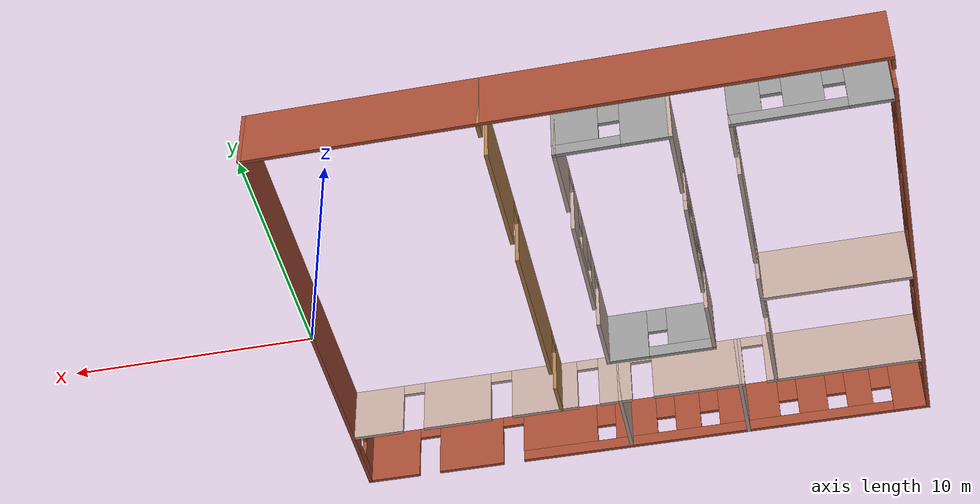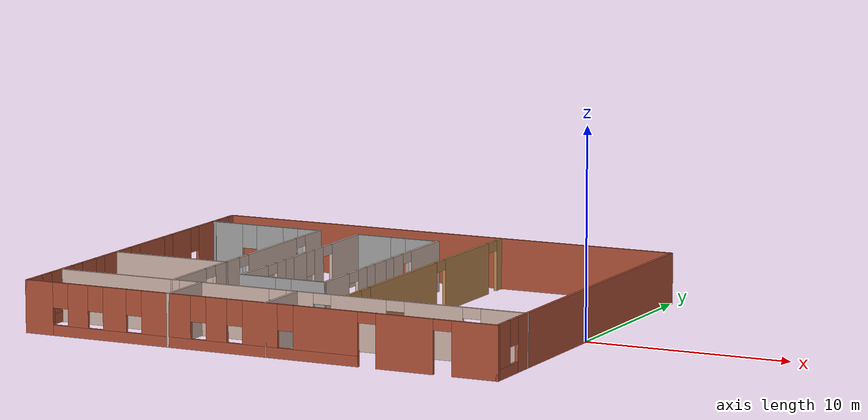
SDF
<?xml version='1.0'?>
<sdf version='1.6'>
  <model name='Building'>
    <pose frame=''>-12.0036 0.25 0 0 -0 0</pose>
    <link name='Wall_0'>
      <pose frame=''>-11.9964 0 0 0 -0 1.5708</pose>
      <visual name='Wall_0_Visual_0'>
        <pose frame=''>-9.18969 0 1.25 0 -0 0</pose>
        <geometry>
          <box>
            <size>1.27061 0.15 2.5</size>
          </box>
        </geometry>
        <material>
          <script>
            <uri>file://media/materials/scripts/gazebo.material</uri>
            <name>Gazebo/Bricks</name>
          </script>
          <ambient>0.760784 0.662745 0.627451 1</ambient>
        </material>
        <meta>
          <layer>0</layer>
        </meta>
      </visual>
      <collision name='Wall_0_Collision_0'>
        <geometry>
          <box>
            <size>1.27061 0.15 2.5</size>
          </box>
        </geometry>
        <pose frame=''>-9.18969 0 1.25 0 -0 0</pose>
      </collision>
      <visual name='Wall_0_Visual_1'>
        <pose frame=''>9.51531 0 1.25 0 -0 0</pose>
        <geometry>
          <box>
            <size>0.619384 0.15 2.5</size>
          </box>
        </geometry>
        <material>
          <script>
            <uri>file://media/materials/scripts/gazebo.material</uri>
            <name>Gazebo/Bricks</name>
          </script>
          <ambient>0.760784 0.662745 0.627451 1</ambient>
        </material>
        <meta>
          <layer>0</layer>
        </meta>
      </visual>
      <collision name='Wall_0_Collision_1'>
        <geometry>
          <box>
            <size>0.619384 0.15 2.5</size>
          </box>
        </geometry>
        <pose frame=''>9.51531 0 1.25 0 -0 0</pose>
      </collision>
      <visual name='Wall_0_Visual_2'>
        <pose frame=''>-0.124385 0 0.25 0 -0 0</pose>
        <geometry>
          <box>
            <size>16.86 0.15 0.5</size>
          </box>
        </geometry>
        <material>
          <script>
            <uri>file://media/materials/scripts/gazebo.material</uri>
            <name>Gazebo/Bricks</name>
          </script>
          <ambient>0.760784 0.662745 0.627451 1</ambient>
        </material>
        <meta>
          <layer>0</layer>
        </meta>
      </visual>
      <collision name='Wall_0_Collision_2'>
        <geometry>
          <box>
            <size>16.86 0.15 0.5</size>
          </box>
        </geometry>
        <pose frame=''>-0.124385 0 0.25 0 -0 0</pose>
      </collision>
      <visual name='Wall_0_Visual_3'>
        <pose frame=''>-6.76332 0 1.5 0 -0 0</pose>
        <geometry>
          <box>
            <size>1.98213 0.15 2</size>
          </box>
        </geometry>
        <material>
          <script>
            <uri>file://media/materials/scripts/gazebo.material</uri>
            <name>Gazebo/Bricks</name>
          </script>
          <ambient>0.760784 0.662745 0.627451 1</ambient>
        </material>
        <meta>
          <layer>0</layer>
        </meta>
      </visual>
      <collision name='Wall_0_Collision_3'>
        <geometry>
          <box>
            <size>1.98213 0.15 2</size>
          </box>
        </geometry>
        <pose frame=''>-6.76332 0 1.5 0 -0 0</pose>
      </collision>
      <visual name='Wall_0_Visual_4'>
        <pose frame=''>-4.35571 0 1.5 0 -0 0</pose>
        <geometry>
          <box>
            <size>1.2331 0.15 2</size>
          </box>
        </geometry>
        <material>
          <script>
            <uri>file://media/materials/scripts/gazebo.material</uri>
            <name>Gazebo/Bricks</name>
          </script>
          <ambient>0.760784 0.662745 0.627451 1</ambient>
        </material>
        <meta>
          <layer>0</layer>
        </meta>
      </visual>
      <collision name='Wall_0_Collision_4'>
        <geometry>
          <box>
            <size>1.2331 0.15 2</size>
          </box>
        </geometry>
        <pose frame=''>-4.35571 0 1.5 0 -0 0</pose>
      </collision>
      <visual name='Wall_0_Visual_5'>
        <pose frame=''>-1.68058 0 1.5 0 -0 0</pose>
        <geometry>
          <box>
            <size>2.51715 0.15 2</size>
          </box>
        </geometry>
        <material>
          <script>
            <uri>file://media/materials/scripts/gazebo.material</uri>
            <name>Gazebo/Bricks</name>
          </script>
          <ambient>0.760784 0.662745 0.627451 1</ambient>
        </material>
        <meta>
          <layer>0</layer>
        </meta>
      </visual>
      <collision name='Wall_0_Collision_5'>
        <geometry>
          <box>
            <size>2.51715 0.15 2</size>
          </box>
        </geometry>
        <pose frame=''>-1.68058 0 1.5 0 -0 0</pose>
      </collision>
      <visual name='Wall_0_Visual_6'>
        <pose frame=''>1.55632 0 1.5 0 -0 0</pose>
        <geometry>
          <box>
            <size>2.35665 0.15 2</size>
          </box>
        </geometry>
        <material>
          <script>
            <uri>file://media/materials/scripts/gazebo.material</uri>
            <name>Gazebo/Bricks</name>
          </script>
          <ambient>0.760784 0.662745 0.627451 1</ambient>
        </material>
        <meta>
          <layer>0</layer>
        </meta>
      </visual>
      <collision name='Wall_0_Collision_6'>
        <geometry>
          <box>
            <size>2.35665 0.15 2</size>
          </box>
        </geometry>
        <pose frame=''>1.55632 0 1.5 0 -0 0</pose>
      </collision>
      <visual name='Wall_0_Visual_7'>
        <pose frame=''>4.44545 0 1.5 0 -0 0</pose>
        <geometry>
          <box>
            <size>1.82162 0.15 2</size>
          </box>
        </geometry>
        <material>
          <script>
            <uri>file://media/materials/scripts/gazebo.material</uri>
            <name>Gazebo/Bricks</name>
          </script>
          <ambient>0.760784 0.662745 0.627451 1</ambient>
        </material>
        <meta>
          <layer>0</layer>
        </meta>
      </visual>
      <collision name='Wall_0_Collision_7'>
        <geometry>
          <box>
            <size>1.82162 0.15 2</size>
          </box>
        </geometry>
        <pose frame=''>4.44545 0 1.5 0 -0 0</pose>
      </collision>
      <visual name='Wall_0_Visual_8'>
        <pose frame=''>7.23094 0 1.5 0 -0 0</pose>
        <geometry>
          <box>
            <size>2.14935 0.15 2</size>
          </box>
        </geometry>
        <material>
          <script>
            <uri>file://media/materials/scripts/gazebo.material</uri>
            <name>Gazebo/Bricks</name>
          </script>
          <ambient>0.760784 0.662745 0.627451 1</ambient>
        </material>
        <meta>
          <layer>0</layer>
        </meta>
      </visual>
      <collision name='Wall_0_Collision_8'>
        <geometry>
          <box>
            <size>2.14935 0.15 2</size>
          </box>
        </geometry>
        <pose frame=''>7.23094 0 1.5 0 -0 0</pose>
      </collision>
      <visual name='Wall_0_Visual_9'>
        <pose frame=''>-8.15439 0 1.9 0 -0 0</pose>
        <geometry>
          <box>
            <size>0.8 0.15 1.2</size>
          </box>
        </geometry>
        <material>
          <script>
            <uri>file://media/materials/scripts/gazebo.material</uri>
            <name>Gazebo/Bricks</name>
          </script>
          <ambient>0.760784 0.662745 0.627451 1</ambient>
        </material>
        <meta>
          <layer>0</layer>
        </meta>
      </visual>
      <collision name='Wall_0_Collision_9'>
        <geometry>
          <box>
            <size>0.8 0.15 1.2</size>
          </box>
        </geometry>
        <pose frame=''>-8.15439 0 1.9 0 -0 0</pose>
      </collision>
      <visual name='Wall_0_Visual_10'>
        <pose frame=''>-5.37226 0 1.9 0 -0 0</pose>
        <geometry>
          <box>
            <size>0.8 0.15 1.2</size>
          </box>
        </geometry>
        <material>
          <script>
            <uri>file://media/materials/scripts/gazebo.material</uri>
            <name>Gazebo/Bricks</name>
          </script>
          <ambient>0.760784 0.662745 0.627451 1</ambient>
        </material>
        <meta>
          <layer>0</layer>
        </meta>
      </visual>
      <collision name='Wall_0_Collision_10'>
        <geometry>
          <box>
            <size>0.8 0.15 1.2</size>
          </box>
        </geometry>
        <pose frame=''>-5.37226 0 1.9 0 -0 0</pose>
      </collision>
      <visual name='Wall_0_Visual_11'>
        <pose frame=''>-3.33916 0 1.9 0 -0 0</pose>
        <geometry>
          <box>
            <size>0.8 0.15 1.2</size>
          </box>
        </geometry>
        <material>
          <script>
            <uri>file://media/materials/scripts/gazebo.material</uri>
            <name>Gazebo/Bricks</name>
          </script>
          <ambient>0.760784 0.662745 0.627451 1</ambient>
        </material>
        <meta>
          <layer>0</layer>
        </meta>
      </visual>
      <collision name='Wall_0_Collision_11'>
        <geometry>
          <box>
            <size>0.8 0.15 1.2</size>
          </box>
        </geometry>
        <pose frame=''>-3.33916 0 1.9 0 -0 0</pose>
      </collision>
      <visual name='Wall_0_Visual_12'>
        <pose frame=''>-0.022006 0 1.9 0 -0 0</pose>
        <geometry>
          <box>
            <size>0.8 0.15 1.2</size>
          </box>
        </geometry>
        <material>
          <script>
            <uri>file://media/materials/scripts/gazebo.material</uri>
            <name>Gazebo/Bricks</name>
          </script>
          <ambient>0.760784 0.662745 0.627451 1</ambient>
        </material>
        <meta>
          <layer>0</layer>
        </meta>
      </visual>
      <collision name='Wall_0_Collision_12'>
        <geometry>
          <box>
            <size>0.8 0.15 1.2</size>
          </box>
        </geometry>
        <pose frame=''>-0.022006 0 1.9 0 -0 0</pose>
      </collision>
      <visual name='Wall_0_Visual_13'>
        <pose frame=''>3.13464 0 1.9 0 -0 0</pose>
        <geometry>
          <box>
            <size>0.8 0.15 1.2</size>
          </box>
        </geometry>
        <material>
          <script>
            <uri>file://media/materials/scripts/gazebo.material</uri>
            <name>Gazebo/Bricks</name>
          </script>
          <ambient>0.760784 0.662745 0.627451 1</ambient>
        </material>
        <meta>
          <layer>0</layer>
        </meta>
      </visual>
      <collision name='Wall_0_Collision_13'>
        <geometry>
          <box>
            <size>0.8 0.15 1.2</size>
          </box>
        </geometry>
        <pose frame=''>3.13464 0 1.9 0 -0 0</pose>
      </collision>
      <visual name='Wall_0_Visual_14'>
        <pose frame=''>5.75626 0 1.9 0 -0 0</pose>
        <geometry>
          <box>
            <size>0.8 0.15 1.2</size>
          </box>
        </geometry>
        <material>
          <script>
            <uri>file://media/materials/scripts/gazebo.material</uri>
            <name>Gazebo/Bricks</name>
          </script>
          <ambient>0.760784 0.662745 0.627451 1</ambient>
        </material>
        <meta>
          <layer>0</layer>
        </meta>
      </visual>
      <collision name='Wall_0_Collision_14'>
        <geometry>
          <box>
            <size>0.8 0.15 1.2</size>
          </box>
        </geometry>
        <pose frame=''>5.75626 0 1.9 0 -0 0</pose>
      </collision>
      <visual name='Wall_0_Visual_15'>
        <pose frame=''>8.75562 0 2.25 0 -0 0</pose>
        <geometry>
          <box>
            <size>0.9 0.15 0.5</size>
          </box>
        </geometry>
        <material>
          <script>
            <uri>file://media/materials/scripts/gazebo.material</uri>
            <name>Gazebo/Bricks</name>
          </script>
          <ambient>0.760784 0.662745 0.627451 1</ambient>
        </material>
        <meta>
          <layer>0</layer>
        </meta>
      </visual>
      <collision name='Wall_0_Collision_15'>
        <geometry>
          <box>
            <size>0.9 0.15 0.5</size>
          </box>
        </geometry>
        <pose frame=''>8.75562 0 2.25 0 -0 0</pose>
      </collision>
    </link>
    <link name='Wall_12'>
      <pose frame=''>3.00359 1.5 0 0 -0 1.5708</pose>
      <visual name='Wall_12_Visual_0'>
        <pose frame=''>-7.57545 0 1.25 0 -0 0</pose>
        <geometry>
          <box>
            <size>1.49911 0.15 2.5</size>
          </box>
        </geometry>
        <material>
          <script>
            <uri>file://media/materials/scripts/gazebo.material</uri>
            <name>Gazebo/Wood</name>
          </script>
          <ambient>0.760784 0.662745 0.627451 1</ambient>
        </material>
        <meta>
          <layer>0</layer>
        </meta>
      </visual>
      <collision name='Wall_12_Collision_0'>
        <geometry>
          <box>
            <size>1.49911 0.15 2.5</size>
          </box>
        </geometry>
        <pose frame=''>-7.57545 0 1.25 0 -0 0</pose>
      </collision>
      <visual name='Wall_12_Visual_1'>
        <pose frame=''>-2.46788 0 1.25 0 -0 0</pose>
        <geometry>
          <box>
            <size>6.91602 0.15 2.5</size>
          </box>
        </geometry>
        <material>
          <script>
            <uri>file://media/materials/scripts/gazebo.material</uri>
            <name>Gazebo/Wood</name>
          </script>
          <ambient>0.760784 0.662745 0.627451 1</ambient>
        </material>
        <meta>
          <layer>0</layer>
        </meta>
      </visual>
      <collision name='Wall_12_Collision_1'>
        <geometry>
          <box>
            <size>6.91602 0.15 2.5</size>
          </box>
        </geometry>
        <pose frame=''>-2.46788 0 1.25 0 -0 0</pose>
      </collision>
      <visual name='Wall_12_Visual_2'>
        <pose frame=''>4.30135 0 1.25 0 -0 0</pose>
        <geometry>
          <box>
            <size>4.82244 0.15 2.5</size>
          </box>
        </geometry>
        <material>
          <script>
            <uri>file://media/materials/scripts/gazebo.material</uri>
            <name>Gazebo/Wood</name>
          </script>
          <ambient>0.760784 0.662745 0.627451 1</ambient>
        </material>
        <meta>
          <layer>0</layer>
        </meta>
      </visual>
      <collision name='Wall_12_Collision_2'>
        <geometry>
          <box>
            <size>4.82244 0.15 2.5</size>
          </box>
        </geometry>
        <pose frame=''>4.30135 0 1.25 0 -0 0</pose>
      </collision>
      <visual name='Wall_12_Visual_3'>
        <pose frame=''>7.96878 0 1.25 0 -0 0</pose>
        <geometry>
          <box>
            <size>0.712432 0.15 2.5</size>
          </box>
        </geometry>
        <material>
          <script>
            <uri>file://media/materials/scripts/gazebo.material</uri>
            <name>Gazebo/Wood</name>
          </script>
          <ambient>0.760784 0.662745 0.627451 1</ambient>
        </material>
        <meta>
          <layer>0</layer>
        </meta>
      </visual>
      <collision name='Wall_12_Collision_3'>
        <geometry>
          <box>
            <size>0.712432 0.15 2.5</size>
          </box>
        </geometry>
        <pose frame=''>7.96878 0 1.25 0 -0 0</pose>
      </collision>
      <visual name='Wall_12_Visual_4'>
        <pose frame=''>-6.37589 0 2.25 0 -0 0</pose>
        <geometry>
          <box>
            <size>0.9 0.15 0.5</size>
          </box>
        </geometry>
        <material>
          <script>
            <uri>file://media/materials/scripts/gazebo.material</uri>
            <name>Gazebo/Wood</name>
          </script>
          <ambient>0.760784 0.662745 0.627451 1</ambient>
        </material>
        <meta>
          <layer>0</layer>
        </meta>
      </visual>
      <collision name='Wall_12_Collision_4'>
        <geometry>
          <box>
            <size>0.9 0.15 0.5</size>
          </box>
        </geometry>
        <pose frame=''>-6.37589 0 2.25 0 -0 0</pose>
      </collision>
      <visual name='Wall_12_Visual_5'>
        <pose frame=''>1.44013 0 2.25 0 -0 0</pose>
        <geometry>
          <box>
            <size>0.9 0.15 0.5</size>
          </box>
        </geometry>
        <material>
          <script>
            <uri>file://media/materials/scripts/gazebo.material</uri>
            <name>Gazebo/Wood</name>
          </script>
          <ambient>0.760784 0.662745 0.627451 1</ambient>
        </material>
        <meta>
          <layer>0</layer>
        </meta>
      </visual>
      <collision name='Wall_12_Collision_5'>
        <geometry>
          <box>
            <size>0.9 0.15 0.5</size>
          </box>
        </geometry>
        <pose frame=''>1.44013 0 2.25 0 -0 0</pose>
      </collision>
      <visual name='Wall_12_Visual_6'>
        <pose frame=''>7.16257 0 2.25 0 -0 0</pose>
        <geometry>
          <box>
            <size>0.9 0.15 0.5</size>
          </box>
        </geometry>
        <material>
          <script>
            <uri>file://media/materials/scripts/gazebo.material</uri>
            <name>Gazebo/Wood</name>
          </script>
          <ambient>0.760784 0.662745 0.627451 1</ambient>
        </material>
        <meta>
          <layer>0</layer>
        </meta>
      </visual>
      <collision name='Wall_12_Collision_6'>
        <geometry>
          <box>
            <size>0.9 0.15 0.5</size>
          </box>
        </geometry>
        <pose frame=''>7.16257 0 2.25 0 -0 0</pose>
      </collision>
    </link>
    <link name='Wall_14'>
      <collision name='Wall_14_Collision'>
        <geometry>
          <box>
            <size>3.15 0.15 2.5</size>
          </box>
        </geometry>
        <pose frame=''>0 0 1.25 0 -0 0</pose>
      </collision>
      <visual name='Wall_14_Visual'>
        <pose frame=''>0 0 1.25 0 -0 0</pose>
        <geometry>
          <box>
            <size>3.15 0.15 2.5</size>
          </box>
        </geometry>
        <material>
          <script>
            <uri>file://media/materials/scripts/gazebo.material</uri>
            <name>Gazebo/Grey</name>
          </script>
          <ambient>0.760784 0.662745 0.627451 1</ambient>
        </material>
        <meta>
          <layer>0</layer>
        </meta>
      </visual>
      <pose frame=''>-4.49641 -8.25 0 0 -0 1.5708</pose>
    </link>
    <link name='Wall_16'>
      <collision name='Wall_16_Collision'>
        <geometry>
          <box>
            <size>3.15 0.15 2.5</size>
          </box>
        </geometry>
        <pose frame=''>0 0 1.25 0 -0 0</pose>
      </collision>
      <visual name='Wall_16_Visual'>
        <pose frame=''>0 0 1.25 0 -0 0</pose>
        <geometry>
          <box>
            <size>3.15 0.15 2.5</size>
          </box>
        </geometry>
        <material>
          <script>
            <uri>file://media/materials/scripts/gazebo.material</uri>
            <name>Gazebo/Grey</name>
          </script>
          <ambient>0.760784 0.662745 0.627451 1</ambient>
        </material>
        <meta>
          <layer>0</layer>
        </meta>
      </visual>
      <pose frame=''>0.50359 -8.25 0 0 -0 1.5708</pose>
    </link>
    <link name='Wall_18'>
      <pose frame=''>-5.99641 0.5 0 0 0 -1.5708</pose>
      <visual name='Wall_18_Visual_0'>
        <pose frame=''>-6.48888 0 1.25 0 -0 0</pose>
        <geometry>
          <box>
            <size>1.67224 0.15 2.5</size>
          </box>
        </geometry>
        <material>
          <script>
            <uri>file://media/materials/scripts/gazebo.material</uri>
            <name>Gazebo/Grey</name>
          </script>
          <ambient>0.760784 0.662745 0.627451 1</ambient>
        </material>
        <meta>
          <layer>0</layer>
        </meta>
      </visual>
      <collision name='Wall_18_Collision_0'>
        <geometry>
          <box>
            <size>1.67224 0.15 2.5</size>
          </box>
        </geometry>
        <pose frame=''>-6.48888 0 1.25 0 -0 0</pose>
      </collision>
      <visual name='Wall_18_Visual_1'>
        <pose frame=''>-2.31363 0 1.25 0 -0 0</pose>
        <geometry>
          <box>
            <size>4.87827 0.15 2.5</size>
          </box>
        </geometry>
        <material>
          <script>
            <uri>file://media/materials/scripts/gazebo.material</uri>
            <name>Gazebo/Grey</name>
          </script>
          <ambient>0.760784 0.662745 0.627451 1</ambient>
        </material>
        <meta>
          <layer>0</layer>
        </meta>
      </visual>
      <collision name='Wall_18_Collision_1'>
        <geometry>
          <box>
            <size>4.87827 0.15 2.5</size>
          </box>
        </geometry>
        <pose frame=''>-2.31363 0 1.25 0 -0 0</pose>
      </collision>
      <visual name='Wall_18_Visual_2'>
        <pose frame=''>2.18058 0 1.25 0 -0 0</pose>
        <geometry>
          <box>
            <size>2.31015 0.15 2.5</size>
          </box>
        </geometry>
        <material>
          <script>
            <uri>file://media/materials/scripts/gazebo.material</uri>
            <name>Gazebo/Grey</name>
          </script>
          <ambient>0.760784 0.662745 0.627451 1</ambient>
        </material>
        <meta>
          <layer>0</layer>
        </meta>
      </visual>
      <collision name='Wall_18_Collision_2'>
        <geometry>
          <box>
            <size>2.31015 0.15 2.5</size>
          </box>
        </geometry>
        <pose frame=''>2.18058 0 1.25 0 -0 0</pose>
      </collision>
      <visual name='Wall_18_Visual_3'>
        <pose frame=''>5.78033 0 1.25 0 -0 0</pose>
        <geometry>
          <box>
            <size>3.08934 0.15 2.5</size>
          </box>
        </geometry>
        <material>
          <script>
            <uri>file://media/materials/scripts/gazebo.material</uri>
            <name>Gazebo/Grey</name>
          </script>
          <ambient>0.760784 0.662745 0.627451 1</ambient>
        </material>
        <meta>
          <layer>0</layer>
        </meta>
      </visual>
      <collision name='Wall_18_Collision_3'>
        <geometry>
          <box>
            <size>3.08934 0.15 2.5</size>
          </box>
        </geometry>
        <pose frame=''>5.78033 0 1.25 0 -0 0</pose>
      </collision>
      <visual name='Wall_18_Visual_4'>
        <pose frame=''>-5.20276 0 2.25 0 -0 0</pose>
        <geometry>
          <box>
            <size>0.9 0.15 0.5</size>
          </box>
        </geometry>
        <material>
          <script>
            <uri>file://media/materials/scripts/gazebo.material</uri>
            <name>Gazebo/Grey</name>
          </script>
          <ambient>0.760784 0.662745 0.627451 1</ambient>
        </material>
        <meta>
          <layer>0</layer>
        </meta>
      </visual>
      <collision name='Wall_18_Collision_4'>
        <geometry>
          <box>
            <size>0.9 0.15 0.5</size>
          </box>
        </geometry>
        <pose frame=''>-5.20276 0 2.25 0 -0 0</pose>
      </collision>
      <visual name='Wall_18_Visual_5'>
        <pose frame=''>0.575509 0 2.25 0 -0 0</pose>
        <geometry>
          <box>
            <size>0.9 0.15 0.5</size>
          </box>
        </geometry>
        <material>
          <script>
            <uri>file://media/materials/scripts/gazebo.material</uri>
            <name>Gazebo/Grey</name>
          </script>
          <ambient>0.760784 0.662745 0.627451 1</ambient>
        </material>
        <meta>
          <layer>0</layer>
        </meta>
      </visual>
      <collision name='Wall_18_Collision_5'>
        <geometry>
          <box>
            <size>0.9 0.15 0.5</size>
          </box>
        </geometry>
        <pose frame=''>0.575509 0 2.25 0 -0 0</pose>
      </collision>
      <visual name='Wall_18_Visual_6'>
        <pose frame=''>3.78566 0 2.25 0 -0 0</pose>
        <geometry>
          <box>
            <size>0.9 0.15 0.5</size>
          </box>
        </geometry>
        <material>
          <script>
            <uri>file://media/materials/scripts/gazebo.material</uri>
            <name>Gazebo/Grey</name>
          </script>
          <ambient>0.760784 0.662745 0.627451 1</ambient>
        </material>
        <meta>
          <layer>0</layer>
        </meta>
      </visual>
      <collision name='Wall_18_Collision_6'>
        <geometry>
          <box>
            <size>0.9 0.15 0.5</size>
          </box>
        </geometry>
        <pose frame=''>3.78566 0 2.25 0 -0 0</pose>
      </collision>
    </link>
    <link name='Wall_2'>
      <collision name='Wall_2_Collision'>
        <geometry>
          <box>
            <size>24.15 0.15 2.5</size>
          </box>
        </geometry>
        <pose frame=''>0 0 1.25 0 -0 0</pose>
      </collision>
      <visual name='Wall_2_Visual'>
        <pose frame=''>0 0 1.25 0 -0 0</pose>
        <geometry>
          <box>
            <size>24.15 0.15 2.5</size>
          </box>
        </geometry>
        <material>
          <script>
            <uri>file://media/materials/scripts/gazebo.material</uri>
            <name>Gazebo/Bricks</name>
          </script>
          <ambient>0.760784 0.662745 0.627451 1</ambient>
        </material>
        <meta>
          <layer>0</layer>
        </meta>
      </visual>
      <pose frame=''>0.00359 9.75 0 0 -0 3.14159</pose>
    </link>
    <link name='Wall_20'>
      <collision name='Wall_20_Collision'>
        <geometry>
          <box>
            <size>0.29021 0.15 2.5</size>
          </box>
        </geometry>
        <pose frame=''>0 0 1.25 0 -0 0</pose>
      </collision>
      <visual name='Wall_20_Visual'>
        <pose frame=''>0 0 1.25 0 -0 0</pose>
        <geometry>
          <box>
            <size>0.29021 0.15 2.5</size>
          </box>
        </geometry>
        <material>
          <script>
            <uri>file://media/materials/scripts/gazebo.material</uri>
            <name>Gazebo/Grey</name>
          </script>
          <ambient>1 1 1 1</ambient>
        </material>
        <meta>
          <layer>0</layer>
        </meta>
      </visual>
      <pose frame=''>-11.9267 7.74293 0 0 -0 3.04054</pose>
    </link>
    <link name='Wall_21'>
      <pose frame=''>-8.99641 7.75 0 0 -0 0</pose>
      <visual name='Wall_21_Visual_0'>
        <pose frame=''>-2.17796 0 1.25 0 -0 0</pose>
        <geometry>
          <box>
            <size>1.79409 0.15 2.5</size>
          </box>
        </geometry>
        <material>
          <script>
            <uri>file://media/materials/scripts/gazebo.material</uri>
            <name>Gazebo/Grey</name>
          </script>
          <ambient>1 1 1 1</ambient>
        </material>
        <meta>
          <layer>0</layer>
        </meta>
      </visual>
      <collision name='Wall_21_Collision_0'>
        <geometry>
          <box>
            <size>1.79409 0.15 2.5</size>
          </box>
        </geometry>
        <pose frame=''>-2.17796 0 1.25 0 -0 0</pose>
      </collision>
      <visual name='Wall_21_Visual_1'>
        <pose frame=''>0.897044 0 0.25 0 -0 0</pose>
        <geometry>
          <box>
            <size>4.35591 0.15 0.5</size>
          </box>
        </geometry>
        <material>
          <script>
            <uri>file://media/materials/scripts/gazebo.material</uri>
            <name>Gazebo/Grey</name>
          </script>
          <ambient>1 1 1 1</ambient>
        </material>
        <meta>
          <layer>0</layer>
        </meta>
      </visual>
      <collision name='Wall_21_Collision_1'>
        <geometry>
          <box>
            <size>4.35591 0.15 0.5</size>
          </box>
        </geometry>
        <pose frame=''>0.897044 0 0.25 0 -0 0</pose>
      </collision>
      <visual name='Wall_21_Visual_2'>
        <pose frame=''>0.269391 0 1.5 0 -0 0</pose>
        <geometry>
          <box>
            <size>1.50061 0.15 2</size>
          </box>
        </geometry>
        <material>
          <script>
            <uri>file://media/materials/scripts/gazebo.material</uri>
            <name>Gazebo/Grey</name>
          </script>
          <ambient>1 1 1 1</ambient>
        </material>
        <meta>
          <layer>0</layer>
        </meta>
      </visual>
      <collision name='Wall_21_Collision_2'>
        <geometry>
          <box>
            <size>1.50061 0.15 2</size>
          </box>
        </geometry>
        <pose frame=''>0.269391 0 1.5 0 -0 0</pose>
      </collision>
      <visual name='Wall_21_Visual_3'>
        <pose frame=''>2.44735 0 1.5 0 -0 0</pose>
        <geometry>
          <box>
            <size>1.2553 0.15 2</size>
          </box>
        </geometry>
        <material>
          <script>
            <uri>file://media/materials/scripts/gazebo.material</uri>
            <name>Gazebo/Grey</name>
          </script>
          <ambient>1 1 1 1</ambient>
        </material>
        <meta>
          <layer>0</layer>
        </meta>
      </visual>
      <collision name='Wall_21_Collision_3'>
        <geometry>
          <box>
            <size>1.2553 0.15 2</size>
          </box>
        </geometry>
        <pose frame=''>2.44735 0 1.5 0 -0 0</pose>
      </collision>
      <visual name='Wall_21_Visual_4'>
        <pose frame=''>-0.880913 0 1.9 0 -0 0</pose>
        <geometry>
          <box>
            <size>0.8 0.15 1.2</size>
          </box>
        </geometry>
        <material>
          <script>
            <uri>file://media/materials/scripts/gazebo.material</uri>
            <name>Gazebo/Grey</name>
          </script>
          <ambient>1 1 1 1</ambient>
        </material>
        <meta>
          <layer>0</layer>
        </meta>
      </visual>
      <collision name='Wall_21_Collision_4'>
        <geometry>
          <box>
            <size>0.8 0.15 1.2</size>
          </box>
        </geometry>
        <pose frame=''>-0.880913 0 1.9 0 -0 0</pose>
      </collision>
      <visual name='Wall_21_Visual_5'>
        <pose frame=''>1.41969 0 1.9 0 -0 0</pose>
        <geometry>
          <box>
            <size>0.8 0.15 1.2</size>
          </box>
        </geometry>
        <material>
          <script>
            <uri>file://media/materials/scripts/gazebo.material</uri>
            <name>Gazebo/Grey</name>
          </script>
          <ambient>1 1 1 1</ambient>
        </material>
        <meta>
          <layer>0</layer>
        </meta>
      </visual>
      <collision name='Wall_21_Collision_5'>
        <geometry>
          <box>
            <size>0.8 0.15 1.2</size>
          </box>
        </geometry>
        <pose frame=''>1.41969 0 1.9 0 -0 0</pose>
      </collision>
    </link>
    <link name='Wall_23'>
      <collision name='Wall_23_Collision'>
        <geometry>
          <box>
            <size>6.15 0.15 2.5</size>
          </box>
        </geometry>
        <pose frame=''>0 0 1.25 0 -0 0</pose>
      </collision>
      <visual name='Wall_23_Visual'>
        <pose frame=''>0 0 1.25 0 -0 0</pose>
        <geometry>
          <box>
            <size>6.15 0.15 2.5</size>
          </box>
        </geometry>
        <material>
          <script>
            <uri>file://media/materials/scripts/gazebo.material</uri>
            <name>Gazebo/Grey</name>
          </script>
          <ambient>0.760784 0.662745 0.627451 1</ambient>
        </material>
        <meta>
          <layer>0</layer>
        </meta>
      </visual>
      <pose frame=''>-8.99641 -1.75 0 0 -0 0</pose>
    </link>
    <link name='Wall_25'>
      <pose frame=''>-1.60304 7.62885 0 0 -0 0</pose>
      <visual name='Wall_25_Visual_0'>
        <pose frame=''>-1.28892 0 1.25 0 -0 0</pose>
        <geometry>
          <box>
            <size>1.92216 0.15 2.5</size>
          </box>
        </geometry>
        <material>
          <script>
            <uri>file://media/materials/scripts/gazebo.material</uri>
            <name>Gazebo/Grey</name>
          </script>
          <ambient>1 1 1 1</ambient>
        </material>
        <meta>
          <layer>0</layer>
        </meta>
      </visual>
      <collision name='Wall_25_Collision_0'>
        <geometry>
          <box>
            <size>1.92216 0.15 2.5</size>
          </box>
        </geometry>
        <pose frame=''>-1.28892 0 1.25 0 -0 0</pose>
      </collision>
      <visual name='Wall_25_Visual_1'>
        <pose frame=''>0.961079 0 0.25 0 -0 0</pose>
        <geometry>
          <box>
            <size>2.57784 0.15 0.5</size>
          </box>
        </geometry>
        <material>
          <script>
            <uri>file://media/materials/scripts/gazebo.material</uri>
            <name>Gazebo/Grey</name>
          </script>
          <ambient>1 1 1 1</ambient>
        </material>
        <meta>
          <layer>0</layer>
        </meta>
      </visual>
      <collision name='Wall_25_Collision_1'>
        <geometry>
          <box>
            <size>2.57784 0.15 0.5</size>
          </box>
        </geometry>
        <pose frame=''>0.961079 0 0.25 0 -0 0</pose>
      </collision>
      <visual name='Wall_25_Visual_2'>
        <pose frame=''>1.36108 0 1.5 0 -0 0</pose>
        <geometry>
          <box>
            <size>1.77784 0.15 2</size>
          </box>
        </geometry>
        <material>
          <script>
            <uri>file://media/materials/scripts/gazebo.material</uri>
            <name>Gazebo/Grey</name>
          </script>
          <ambient>1 1 1 1</ambient>
        </material>
        <meta>
          <layer>0</layer>
        </meta>
      </visual>
      <collision name='Wall_25_Collision_2'>
        <geometry>
          <box>
            <size>1.77784 0.15 2</size>
          </box>
        </geometry>
        <pose frame=''>1.36108 0 1.5 0 -0 0</pose>
      </collision>
      <visual name='Wall_25_Visual_3'>
        <pose frame=''>0.072158 0 1.9 0 -0 0</pose>
        <geometry>
          <box>
            <size>0.8 0.15 1.2</size>
          </box>
        </geometry>
        <material>
          <script>
            <uri>file://media/materials/scripts/gazebo.material</uri>
            <name>Gazebo/Grey</name>
          </script>
          <ambient>1 1 1 1</ambient>
        </material>
        <meta>
          <layer>0</layer>
        </meta>
      </visual>
      <collision name='Wall_25_Collision_3'>
        <geometry>
          <box>
            <size>0.8 0.15 1.2</size>
          </box>
        </geometry>
        <pose frame=''>0.072158 0 1.9 0 -0 0</pose>
      </collision>
    </link>
    <link name='Wall_26'>
      <pose frame=''>0.571963 1.70385 0 0 0 -1.5708</pose>
      <visual name='Wall_26_Visual_0'>
        <pose frame=''>-4.47121 0 1.25 0 -0 0</pose>
        <geometry>
          <box>
            <size>3.05758 0.15 2.5</size>
          </box>
        </geometry>
        <material>
          <script>
            <uri>file://media/materials/scripts/gazebo.material</uri>
            <name>Gazebo/Grey</name>
          </script>
          <ambient>0.760784 0.662745 0.627451 1</ambient>
        </material>
        <meta>
          <layer>0</layer>
        </meta>
      </visual>
      <collision name='Wall_26_Collision_0'>
        <geometry>
          <box>
            <size>3.05758 0.15 2.5</size>
          </box>
        </geometry>
        <pose frame=''>-4.47121 0 1.25 0 -0 0</pose>
      </collision>
      <visual name='Wall_26_Visual_1'>
        <pose frame=''>-1.53694 0 1.25 0 -0 0</pose>
        <geometry>
          <box>
            <size>1.01096 0.15 2.5</size>
          </box>
        </geometry>
        <material>
          <script>
            <uri>file://media/materials/scripts/gazebo.material</uri>
            <name>Gazebo/Grey</name>
          </script>
          <ambient>0.760784 0.662745 0.627451 1</ambient>
        </material>
        <meta>
          <layer>0</layer>
        </meta>
      </visual>
      <collision name='Wall_26_Collision_1'>
        <geometry>
          <box>
            <size>1.01096 0.15 2.5</size>
          </box>
        </geometry>
        <pose frame=''>-1.53694 0 1.25 0 -0 0</pose>
      </collision>
      <visual name='Wall_26_Visual_2'>
        <pose frame=''>4.77022 0 1.25 0 -0 0</pose>
        <geometry>
          <box>
            <size>2.45955 0.15 2.5</size>
          </box>
        </geometry>
        <material>
          <script>
            <uri>file://media/materials/scripts/gazebo.material</uri>
            <name>Gazebo/Grey</name>
          </script>
          <ambient>0.760784 0.662745 0.627451 1</ambient>
        </material>
        <meta>
          <layer>0</layer>
        </meta>
      </visual>
      <collision name='Wall_26_Collision_2'>
        <geometry>
          <box>
            <size>2.45955 0.15 2.5</size>
          </box>
        </geometry>
        <pose frame=''>4.77022 0 1.25 0 -0 0</pose>
      </collision>
      <visual name='Wall_26_Visual_3'>
        <pose frame=''>0.804492 0 0.25 0 -0 0</pose>
        <geometry>
          <box>
            <size>3.67191 0.15 0.5</size>
          </box>
        </geometry>
        <material>
          <script>
            <uri>file://media/materials/scripts/gazebo.material</uri>
            <name>Gazebo/Grey</name>
          </script>
          <ambient>0.760784 0.662745 0.627451 1</ambient>
        </material>
        <meta>
          <layer>0</layer>
        </meta>
      </visual>
      <collision name='Wall_26_Collision_3'>
        <geometry>
          <box>
            <size>3.67191 0.15 0.5</size>
          </box>
        </geometry>
        <pose frame=''>0.804492 0 0.25 0 -0 0</pose>
      </collision>
      <visual name='Wall_26_Visual_4'>
        <pose frame=''>0.345537 0 1.5 0 -0 0</pose>
        <geometry>
          <box>
            <size>1.154 0.15 2</size>
          </box>
        </geometry>
        <material>
          <script>
            <uri>file://media/materials/scripts/gazebo.material</uri>
            <name>Gazebo/Grey</name>
          </script>
          <ambient>0.760784 0.662745 0.627451 1</ambient>
        </material>
        <meta>
          <layer>0</layer>
        </meta>
      </visual>
      <collision name='Wall_26_Collision_4'>
        <geometry>
          <box>
            <size>1.154 0.15 2</size>
          </box>
        </geometry>
        <pose frame=''>0.345537 0 1.5 0 -0 0</pose>
      </collision>
      <visual name='Wall_26_Visual_5'>
        <pose frame=''>2.18149 0 1.5 0 -0 0</pose>
        <geometry>
          <box>
            <size>0.917909 0.15 2</size>
          </box>
        </geometry>
        <material>
          <script>
            <uri>file://media/materials/scripts/gazebo.material</uri>
            <name>Gazebo/Grey</name>
          </script>
          <ambient>0.760784 0.662745 0.627451 1</ambient>
        </material>
        <meta>
          <layer>0</layer>
        </meta>
      </visual>
      <collision name='Wall_26_Collision_5'>
        <geometry>
          <box>
            <size>0.917909 0.15 2</size>
          </box>
        </geometry>
        <pose frame=''>2.18149 0 1.5 0 -0 0</pose>
      </collision>
      <visual name='Wall_26_Visual_6'>
        <pose frame=''>-0.631465 0 1.9 0 -0 0</pose>
        <geometry>
          <box>
            <size>0.8 0.15 1.2</size>
          </box>
        </geometry>
        <material>
          <script>
            <uri>file://media/materials/scripts/gazebo.material</uri>
            <name>Gazebo/Grey</name>
          </script>
          <ambient>0.760784 0.662745 0.627451 1</ambient>
        </material>
        <meta>
          <layer>0</layer>
        </meta>
      </visual>
      <collision name='Wall_26_Collision_6'>
        <geometry>
          <box>
            <size>0.8 0.15 1.2</size>
          </box>
        </geometry>
        <pose frame=''>-0.631465 0 1.9 0 -0 0</pose>
      </collision>
      <visual name='Wall_26_Visual_7'>
        <pose frame=''>1.32254 0 1.9 0 -0 0</pose>
        <geometry>
          <box>
            <size>0.8 0.15 1.2</size>
          </box>
        </geometry>
        <material>
          <script>
            <uri>file://media/materials/scripts/gazebo.material</uri>
            <name>Gazebo/Grey</name>
          </script>
          <ambient>0.760784 0.662745 0.627451 1</ambient>
        </material>
        <meta>
          <layer>0</layer>
        </meta>
      </visual>
      <collision name='Wall_26_Collision_7'>
        <geometry>
          <box>
            <size>0.8 0.15 1.2</size>
          </box>
        </geometry>
        <pose frame=''>1.32254 0 1.9 0 -0 0</pose>
      </collision>
      <visual name='Wall_26_Visual_8'>
        <pose frame=''>-2.49242 0 2.25 0 -0 0</pose>
        <geometry>
          <box>
            <size>0.9 0.15 0.5</size>
          </box>
        </geometry>
        <material>
          <script>
            <uri>file://media/materials/scripts/gazebo.material</uri>
            <name>Gazebo/Grey</name>
          </script>
          <ambient>0.760784 0.662745 0.627451 1</ambient>
        </material>
        <meta>
          <layer>0</layer>
        </meta>
      </visual>
      <collision name='Wall_26_Collision_8'>
        <geometry>
          <box>
            <size>0.9 0.15 0.5</size>
          </box>
        </geometry>
        <pose frame=''>-2.49242 0 2.25 0 -0 0</pose>
      </collision>
      <visual name='Wall_26_Visual_9'>
        <pose frame=''>3.09045 0 2.25 0 -0 0</pose>
        <geometry>
          <box>
            <size>0.9 0.15 0.5</size>
          </box>
        </geometry>
        <material>
          <script>
            <uri>file://media/materials/scripts/gazebo.material</uri>
            <name>Gazebo/Grey</name>
          </script>
          <ambient>0.760784 0.662745 0.627451 1</ambient>
        </material>
        <meta>
          <layer>0</layer>
        </meta>
      </visual>
      <collision name='Wall_26_Collision_9'>
        <geometry>
          <box>
            <size>0.9 0.15 0.5</size>
          </box>
        </geometry>
        <pose frame=''>3.09045 0 2.25 0 -0 0</pose>
      </collision>
    </link>
    <link name='Wall_27'>
      <pose frame=''>-1.60304 -4.22115 0 0 -0 3.14159</pose>
      <visual name='Wall_27_Visual_0'>
        <pose frame=''>-1.36108 0 1.25 0 -0 0</pose>
        <geometry>
          <box>
            <size>1.77784 0.15 2.5</size>
          </box>
        </geometry>
        <material>
          <script>
            <uri>file://media/materials/scripts/gazebo.material</uri>
            <name>Gazebo/Grey</name>
          </script>
          <ambient>1 1 1 1</ambient>
        </material>
        <meta>
          <layer>0</layer>
        </meta>
      </visual>
      <collision name='Wall_27_Collision_0'>
        <geometry>
          <box>
            <size>1.77784 0.15 2.5</size>
          </box>
        </geometry>
        <pose frame=''>-1.36108 0 1.25 0 -0 0</pose>
      </collision>
      <visual name='Wall_27_Visual_1'>
        <pose frame=''>0.888921 0 0.25 0 -0 0</pose>
        <geometry>
          <box>
            <size>2.72216 0.15 0.5</size>
          </box>
        </geometry>
        <material>
          <script>
            <uri>file://media/materials/scripts/gazebo.material</uri>
            <name>Gazebo/Grey</name>
          </script>
          <ambient>1 1 1 1</ambient>
        </material>
        <meta>
          <layer>0</layer>
        </meta>
      </visual>
      <collision name='Wall_27_Collision_1'>
        <geometry>
          <box>
            <size>2.72216 0.15 0.5</size>
          </box>
        </geometry>
        <pose frame=''>0.888921 0 0.25 0 -0 0</pose>
      </collision>
      <visual name='Wall_27_Visual_2'>
        <pose frame=''>1.28892 0 1.5 0 -0 0</pose>
        <geometry>
          <box>
            <size>1.92216 0.15 2</size>
          </box>
        </geometry>
        <material>
          <script>
            <uri>file://media/materials/scripts/gazebo.material</uri>
            <name>Gazebo/Grey</name>
          </script>
          <ambient>1 1 1 1</ambient>
        </material>
        <meta>
          <layer>0</layer>
        </meta>
      </visual>
      <collision name='Wall_27_Collision_2'>
        <geometry>
          <box>
            <size>1.92216 0.15 2</size>
          </box>
        </geometry>
        <pose frame=''>1.28892 0 1.5 0 -0 0</pose>
      </collision>
      <visual name='Wall_27_Visual_3'>
        <pose frame=''>-0.072158 0 1.9 0 -0 0</pose>
        <geometry>
          <box>
            <size>0.8 0.15 1.2</size>
          </box>
        </geometry>
        <material>
          <script>
            <uri>file://media/materials/scripts/gazebo.material</uri>
            <name>Gazebo/Grey</name>
          </script>
          <ambient>1 1 1 1</ambient>
        </material>
        <meta>
          <layer>0</layer>
        </meta>
      </visual>
      <collision name='Wall_27_Collision_3'>
        <geometry>
          <box>
            <size>0.8 0.15 1.2</size>
          </box>
        </geometry>
        <pose frame=''>-0.072158 0 1.9 0 -0 0</pose>
      </collision>
    </link>
    <link name='Wall_28'>
      <pose frame=''>-3.77804 1.70385 0 0 -0 1.5708</pose>
      <visual name='Wall_28_Visual_0'>
        <pose frame=''>-4.7237 0 1.25 0 -0 0</pose>
        <geometry>
          <box>
            <size>2.5526 0.15 2.5</size>
          </box>
        </geometry>
        <material>
          <script>
            <uri>file://media/materials/scripts/gazebo.material</uri>
            <name>Gazebo/Grey</name>
          </script>
          <ambient>0.760784 0.662745 0.627451 1</ambient>
        </material>
        <meta>
          <layer>0</layer>
        </meta>
      </visual>
      <collision name='Wall_28_Collision_0'>
        <geometry>
          <box>
            <size>2.5526 0.15 2.5</size>
          </box>
        </geometry>
        <pose frame=''>-4.7237 0 1.25 0 -0 0</pose>
      </collision>
      <visual name='Wall_28_Visual_1'>
        <pose frame=''>-2.11171 0 1.25 0 -0 0</pose>
        <geometry>
          <box>
            <size>0.871385 0.15 2.5</size>
          </box>
        </geometry>
        <material>
          <script>
            <uri>file://media/materials/scripts/gazebo.material</uri>
            <name>Gazebo/Grey</name>
          </script>
          <ambient>0.760784 0.662745 0.627451 1</ambient>
        </material>
        <meta>
          <layer>0</layer>
        </meta>
      </visual>
      <collision name='Wall_28_Collision_1'>
        <geometry>
          <box>
            <size>0.871385 0.15 2.5</size>
          </box>
        </geometry>
        <pose frame=''>-2.11171 0 1.25 0 -0 0</pose>
      </collision>
      <visual name='Wall_28_Visual_2'>
        <pose frame=''>4.51774 0 1.25 0 -0 0</pose>
        <geometry>
          <box>
            <size>2.96453 0.15 2.5</size>
          </box>
        </geometry>
        <material>
          <script>
            <uri>file://media/materials/scripts/gazebo.material</uri>
            <name>Gazebo/Grey</name>
          </script>
          <ambient>0.760784 0.662745 0.627451 1</ambient>
        </material>
        <meta>
          <layer>0</layer>
        </meta>
      </visual>
      <collision name='Wall_28_Collision_2'>
        <geometry>
          <box>
            <size>2.96453 0.15 2.5</size>
          </box>
        </geometry>
        <pose frame=''>4.51774 0 1.25 0 -0 0</pose>
      </collision>
      <visual name='Wall_28_Visual_3'>
        <pose frame=''>0.229727 0 0.25 0 -0 0</pose>
        <geometry>
          <box>
            <size>3.81148 0.15 0.5</size>
          </box>
        </geometry>
        <material>
          <script>
            <uri>file://media/materials/scripts/gazebo.material</uri>
            <name>Gazebo/Grey</name>
          </script>
          <ambient>0.760784 0.662745 0.627451 1</ambient>
        </material>
        <meta>
          <layer>0</layer>
        </meta>
      </visual>
      <collision name='Wall_28_Collision_3'>
        <geometry>
          <box>
            <size>3.81148 0.15 0.5</size>
          </box>
        </geometry>
        <pose frame=''>0.229727 0 0.25 0 -0 0</pose>
      </collision>
      <visual name='Wall_28_Visual_4'>
        <pose frame=''>-0.229227 0 1.5 0 -0 0</pose>
        <geometry>
          <box>
            <size>1.29358 0.15 2</size>
          </box>
        </geometry>
        <material>
          <script>
            <uri>file://media/materials/scripts/gazebo.material</uri>
            <name>Gazebo/Grey</name>
          </script>
          <ambient>0.760784 0.662745 0.627451 1</ambient>
        </material>
        <meta>
          <layer>0</layer>
        </meta>
      </visual>
      <collision name='Wall_28_Collision_4'>
        <geometry>
          <box>
            <size>1.29358 0.15 2</size>
          </box>
        </geometry>
        <pose frame=''>-0.229227 0 1.5 0 -0 0</pose>
      </collision>
      <visual name='Wall_28_Visual_5'>
        <pose frame=''>1.67651 0 1.5 0 -0 0</pose>
        <geometry>
          <box>
            <size>0.917909 0.15 2</size>
          </box>
        </geometry>
        <material>
          <script>
            <uri>file://media/materials/scripts/gazebo.material</uri>
            <name>Gazebo/Grey</name>
          </script>
          <ambient>0.760784 0.662745 0.627451 1</ambient>
        </material>
        <meta>
          <layer>0</layer>
        </meta>
      </visual>
      <collision name='Wall_28_Collision_5'>
        <geometry>
          <box>
            <size>0.917909 0.15 2</size>
          </box>
        </geometry>
        <pose frame=''>1.67651 0 1.5 0 -0 0</pose>
      </collision>
      <visual name='Wall_28_Visual_6'>
        <pose frame=''>-1.27601 0 1.9 0 -0 0</pose>
        <geometry>
          <box>
            <size>0.8 0.15 1.2</size>
          </box>
        </geometry>
        <material>
          <script>
            <uri>file://media/materials/scripts/gazebo.material</uri>
            <name>Gazebo/Grey</name>
          </script>
          <ambient>0.760784 0.662745 0.627451 1</ambient>
        </material>
        <meta>
          <layer>0</layer>
        </meta>
      </visual>
      <collision name='Wall_28_Collision_6'>
        <geometry>
          <box>
            <size>0.8 0.15 1.2</size>
          </box>
        </geometry>
        <pose frame=''>-1.27601 0 1.9 0 -0 0</pose>
      </collision>
      <visual name='Wall_28_Visual_7'>
        <pose frame=''>0.817561 0 1.9 0 -0 0</pose>
        <geometry>
          <box>
            <size>0.8 0.15 1.2</size>
          </box>
        </geometry>
        <material>
          <script>
            <uri>file://media/materials/scripts/gazebo.material</uri>
            <name>Gazebo/Grey</name>
          </script>
          <ambient>0.760784 0.662745 0.627451 1</ambient>
        </material>
        <meta>
          <layer>0</layer>
        </meta>
      </visual>
      <collision name='Wall_28_Collision_7'>
        <geometry>
          <box>
            <size>0.8 0.15 1.2</size>
          </box>
        </geometry>
        <pose frame=''>0.817561 0 1.9 0 -0 0</pose>
      </collision>
      <visual name='Wall_28_Visual_8'>
        <pose frame=''>-2.9974 0 2.25 0 -0 0</pose>
        <geometry>
          <box>
            <size>0.9 0.15 0.5</size>
          </box>
        </geometry>
        <material>
          <script>
            <uri>file://media/materials/scripts/gazebo.material</uri>
            <name>Gazebo/Grey</name>
          </script>
          <ambient>0.760784 0.662745 0.627451 1</ambient>
        </material>
        <meta>
          <layer>0</layer>
        </meta>
      </visual>
      <collision name='Wall_28_Collision_8'>
        <geometry>
          <box>
            <size>0.9 0.15 0.5</size>
          </box>
        </geometry>
        <pose frame=''>-2.9974 0 2.25 0 -0 0</pose>
      </collision>
      <visual name='Wall_28_Visual_9'>
        <pose frame=''>2.58547 0 2.25 0 -0 0</pose>
        <geometry>
          <box>
            <size>0.9 0.15 0.5</size>
          </box>
        </geometry>
        <material>
          <script>
            <uri>file://media/materials/scripts/gazebo.material</uri>
            <name>Gazebo/Grey</name>
          </script>
          <ambient>0.760784 0.662745 0.627451 1</ambient>
        </material>
        <meta>
          <layer>0</layer>
        </meta>
      </visual>
      <collision name='Wall_28_Collision_9'>
        <geometry>
          <box>
            <size>0.9 0.15 0.5</size>
          </box>
        </geometry>
        <pose frame=''>2.58547 0 2.25 0 -0 0</pose>
      </collision>
    </link>
    <link name='Wall_5'>
      <pose frame=''>0.00359 -9.75 0 0 -0 0</pose>
      <visual name='Wall_5_Visual_0'>
        <pose frame=''>-11.3385 0 1.25 0 -0 0</pose>
        <geometry>
          <box>
            <size>1.47307 0.15 2.5</size>
          </box>
        </geometry>
        <material>
          <script>
            <uri>file://media/materials/scripts/gazebo.material</uri>
            <name>Gazebo/Bricks</name>
          </script>
          <ambient>0.760784 0.662745 0.627451 1</ambient>
        </material>
        <meta>
          <layer>0</layer>
        </meta>
      </visual>
      <collision name='Wall_5_Collision_0'>
        <geometry>
          <box>
            <size>1.47307 0.15 2.5</size>
          </box>
        </geometry>
        <pose frame=''>-11.3385 0 1.25 0 -0 0</pose>
      </collision>
      <visual name='Wall_5_Visual_1'>
        <pose frame=''>7.49117 0 1.25 0 -0 0</pose>
        <geometry>
          <box>
            <size>2.82191 0.15 2.5</size>
          </box>
        </geometry>
        <material>
          <script>
            <uri>file://media/materials/scripts/gazebo.material</uri>
            <name>Gazebo/Bricks</name>
          </script>
          <ambient>0.760784 0.662745 0.627451 1</ambient>
        </material>
        <meta>
          <layer>0</layer>
        </meta>
      </visual>
      <collision name='Wall_5_Collision_1'>
        <geometry>
          <box>
            <size>2.82191 0.15 2.5</size>
          </box>
        </geometry>
        <pose frame=''>7.49117 0 1.25 0 -0 0</pose>
      </collision>
      <visual name='Wall_5_Visual_2'>
        <pose frame=''>10.9386 0 1.25 0 -0 0</pose>
        <geometry>
          <box>
            <size>2.27287 0.15 2.5</size>
          </box>
        </geometry>
        <material>
          <script>
            <uri>file://media/materials/scripts/gazebo.material</uri>
            <name>Gazebo/Bricks</name>
          </script>
          <ambient>0.760784 0.662745 0.627451 1</ambient>
        </material>
        <meta>
          <layer>0</layer>
        </meta>
      </visual>
      <collision name='Wall_5_Collision_2'>
        <geometry>
          <box>
            <size>2.27287 0.15 2.5</size>
          </box>
        </geometry>
        <pose frame=''>10.9386 0 1.25 0 -0 0</pose>
      </collision>
      <visual name='Wall_5_Visual_3'>
        <pose frame=''>-2.71086 0 0.25 0 -0 0</pose>
        <geometry>
          <box>
            <size>15.7821 0.15 0.5</size>
          </box>
        </geometry>
        <material>
          <script>
            <uri>file://media/materials/scripts/gazebo.material</uri>
            <name>Gazebo/Bricks</name>
          </script>
          <ambient>0.760784 0.662745 0.627451 1</ambient>
        </material>
        <meta>
          <layer>0</layer>
        </meta>
      </visual>
      <collision name='Wall_5_Collision_3'>
        <geometry>
          <box>
            <size>15.7821 0.15 0.5</size>
          </box>
        </geometry>
        <pose frame=''>-2.71086 0 0.25 0 -0 0</pose>
      </collision>
      <visual name='Wall_5_Visual_4'>
        <pose frame=''>-9.26563 0 1.5 0 -0 0</pose>
        <geometry>
          <box>
            <size>1.07259 0.15 2</size>
          </box>
        </geometry>
        <material>
          <script>
            <uri>file://media/materials/scripts/gazebo.material</uri>
            <name>Gazebo/Bricks</name>
          </script>
          <ambient>0.760784 0.662745 0.627451 1</ambient>
        </material>
        <meta>
          <layer>0</layer>
        </meta>
      </visual>
      <collision name='Wall_5_Collision_4'>
        <geometry>
          <box>
            <size>1.07259 0.15 2</size>
          </box>
        </geometry>
        <pose frame=''>-9.26563 0 1.5 0 -0 0</pose>
      </collision>
      <visual name='Wall_5_Visual_5'>
        <pose frame=''>-7.31279 0 1.5 0 -0 0</pose>
        <geometry>
          <box>
            <size>1.23309 0.15 2</size>
          </box>
        </geometry>
        <material>
          <script>
            <uri>file://media/materials/scripts/gazebo.material</uri>
            <name>Gazebo/Bricks</name>
          </script>
          <ambient>0.760784 0.662745 0.627451 1</ambient>
        </material>
        <meta>
          <layer>0</layer>
        </meta>
      </visual>
      <collision name='Wall_5_Collision_5'>
        <geometry>
          <box>
            <size>1.23309 0.15 2</size>
          </box>
        </geometry>
        <pose frame=''>-7.31279 0 1.5 0 -0 0</pose>
      </collision>
      <visual name='Wall_5_Visual_6'>
        <pose frame=''>-4.61092 0 1.5 0 -0 0</pose>
        <geometry>
          <box>
            <size>2.57066 0.15 2</size>
          </box>
        </geometry>
        <material>
          <script>
            <uri>file://media/materials/scripts/gazebo.material</uri>
            <name>Gazebo/Bricks</name>
          </script>
          <ambient>0.760784 0.662745 0.627451 1</ambient>
        </material>
        <meta>
          <layer>0</layer>
        </meta>
      </visual>
      <collision name='Wall_5_Collision_6'>
        <geometry>
          <box>
            <size>2.57066 0.15 2</size>
          </box>
        </geometry>
        <pose frame=''>-4.61092 0 1.5 0 -0 0</pose>
      </collision>
      <visual name='Wall_5_Visual_7'>
        <pose frame=''>-1.98929 0 1.5 0 -0 0</pose>
        <geometry>
          <box>
            <size>1.07259 0.15 2</size>
          </box>
        </geometry>
        <material>
          <script>
            <uri>file://media/materials/scripts/gazebo.material</uri>
            <name>Gazebo/Bricks</name>
          </script>
          <ambient>0.760784 0.662745 0.627451 1</ambient>
        </material>
        <meta>
          <layer>0</layer>
        </meta>
      </visual>
      <collision name='Wall_5_Collision_7'>
        <geometry>
          <box>
            <size>1.07259 0.15 2</size>
          </box>
        </geometry>
        <pose frame=''>-1.98929 0 1.5 0 -0 0</pose>
      </collision>
      <visual name='Wall_5_Visual_8'>
        <pose frame=''>0.241555 0 1.5 0 -0 0</pose>
        <geometry>
          <box>
            <size>1.78911 0.15 2</size>
          </box>
        </geometry>
        <material>
          <script>
            <uri>file://media/materials/scripts/gazebo.material</uri>
            <name>Gazebo/Bricks</name>
          </script>
          <ambient>0.760784 0.662745 0.627451 1</ambient>
        </material>
        <meta>
          <layer>0</layer>
        </meta>
      </visual>
      <collision name='Wall_5_Collision_8'>
        <geometry>
          <box>
            <size>1.78911 0.15 2</size>
          </box>
        </geometry>
        <pose frame=''>0.241555 0 1.5 0 -0 0</pose>
      </collision>
      <visual name='Wall_5_Visual_9'>
        <pose frame=''>3.55816 0 1.5 0 -0 0</pose>
        <geometry>
          <box>
            <size>3.2441 0.15 2</size>
          </box>
        </geometry>
        <material>
          <script>
            <uri>file://media/materials/scripts/gazebo.material</uri>
            <name>Gazebo/Bricks</name>
          </script>
          <ambient>0.760784 0.662745 0.627451 1</ambient>
        </material>
        <meta>
          <layer>0</layer>
        </meta>
      </visual>
      <collision name='Wall_5_Collision_9'>
        <geometry>
          <box>
            <size>3.2441 0.15 2</size>
          </box>
        </geometry>
        <pose frame=''>3.55816 0 1.5 0 -0 0</pose>
      </collision>
      <visual name='Wall_5_Visual_10'>
        <pose frame=''>-10.2019 0 1.9 0 -0 0</pose>
        <geometry>
          <box>
            <size>0.8 0.15 1.2</size>
          </box>
        </geometry>
        <material>
          <script>
            <uri>file://media/materials/scripts/gazebo.material</uri>
            <name>Gazebo/Bricks</name>
          </script>
          <ambient>0.760784 0.662745 0.627451 1</ambient>
        </material>
        <meta>
          <layer>0</layer>
        </meta>
      </visual>
      <collision name='Wall_5_Collision_10'>
        <geometry>
          <box>
            <size>0.8 0.15 1.2</size>
          </box>
        </geometry>
        <pose frame=''>-10.2019 0 1.9 0 -0 0</pose>
      </collision>
      <visual name='Wall_5_Visual_11'>
        <pose frame=''>-8.32934 0 1.9 0 -0 0</pose>
        <geometry>
          <box>
            <size>0.8 0.15 1.2</size>
          </box>
        </geometry>
        <material>
          <script>
            <uri>file://media/materials/scripts/gazebo.material</uri>
            <name>Gazebo/Bricks</name>
          </script>
          <ambient>0.760784 0.662745 0.627451 1</ambient>
        </material>
        <meta>
          <layer>0</layer>
        </meta>
      </visual>
      <collision name='Wall_5_Collision_11'>
        <geometry>
          <box>
            <size>0.8 0.15 1.2</size>
          </box>
        </geometry>
        <pose frame=''>-8.32934 0 1.9 0 -0 0</pose>
      </collision>
      <visual name='Wall_5_Visual_12'>
        <pose frame=''>-6.29625 0 1.9 0 -0 0</pose>
        <geometry>
          <box>
            <size>0.8 0.15 1.2</size>
          </box>
        </geometry>
        <material>
          <script>
            <uri>file://media/materials/scripts/gazebo.material</uri>
            <name>Gazebo/Bricks</name>
          </script>
          <ambient>0.760784 0.662745 0.627451 1</ambient>
        </material>
        <meta>
          <layer>0</layer>
        </meta>
      </visual>
      <collision name='Wall_5_Collision_12'>
        <geometry>
          <box>
            <size>0.8 0.15 1.2</size>
          </box>
        </geometry>
        <pose frame=''>-6.29625 0 1.9 0 -0 0</pose>
      </collision>
      <visual name='Wall_5_Visual_13'>
        <pose frame=''>-2.92559 0 1.9 0 -0 0</pose>
        <geometry>
          <box>
            <size>0.8 0.15 1.2</size>
          </box>
        </geometry>
        <material>
          <script>
            <uri>file://media/materials/scripts/gazebo.material</uri>
            <name>Gazebo/Bricks</name>
          </script>
          <ambient>0.760784 0.662745 0.627451 1</ambient>
        </material>
        <meta>
          <layer>0</layer>
        </meta>
      </visual>
      <collision name='Wall_5_Collision_13'>
        <geometry>
          <box>
            <size>0.8 0.15 1.2</size>
          </box>
        </geometry>
        <pose frame=''>-2.92559 0 1.9 0 -0 0</pose>
      </collision>
      <visual name='Wall_5_Visual_14'>
        <pose frame=''>-1.053 0 1.9 0 -0 0</pose>
        <geometry>
          <box>
            <size>0.8 0.15 1.2</size>
          </box>
        </geometry>
        <material>
          <script>
            <uri>file://media/materials/scripts/gazebo.material</uri>
            <name>Gazebo/Bricks</name>
          </script>
          <ambient>0.760784 0.662745 0.627451 1</ambient>
        </material>
        <meta>
          <layer>0</layer>
        </meta>
      </visual>
      <collision name='Wall_5_Collision_14'>
        <geometry>
          <box>
            <size>0.8 0.15 1.2</size>
          </box>
        </geometry>
        <pose frame=''>-1.053 0 1.9 0 -0 0</pose>
      </collision>
      <visual name='Wall_5_Visual_15'>
        <pose frame=''>1.53611 0 1.9 0 -0 0</pose>
        <geometry>
          <box>
            <size>0.8 0.15 1.2</size>
          </box>
        </geometry>
        <material>
          <script>
            <uri>file://media/materials/scripts/gazebo.material</uri>
            <name>Gazebo/Bricks</name>
          </script>
          <ambient>0.760784 0.662745 0.627451 1</ambient>
        </material>
        <meta>
          <layer>0</layer>
        </meta>
      </visual>
      <collision name='Wall_5_Collision_15'>
        <geometry>
          <box>
            <size>0.8 0.15 1.2</size>
          </box>
        </geometry>
        <pose frame=''>1.53611 0 1.9 0 -0 0</pose>
      </collision>
      <visual name='Wall_5_Visual_16'>
        <pose frame=''>9.35213 0 2.25 0 -0 0</pose>
        <geometry>
          <box>
            <size>0.9 0.15 0.5</size>
          </box>
        </geometry>
        <material>
          <script>
            <uri>file://media/materials/scripts/gazebo.material</uri>
            <name>Gazebo/Bricks</name>
          </script>
          <ambient>0.760784 0.662745 0.627451 1</ambient>
        </material>
        <meta>
          <layer>0</layer>
        </meta>
      </visual>
      <collision name='Wall_5_Collision_16'>
        <geometry>
          <box>
            <size>0.9 0.15 0.5</size>
          </box>
        </geometry>
        <pose frame=''>9.35213 0 2.25 0 -0 0</pose>
      </collision>
      <visual name='Wall_5_Visual_17'>
        <pose frame=''>5.63021 0 2.25 0 -0 0</pose>
        <geometry>
          <box>
            <size>0.9 0.15 0.5</size>
          </box>
        </geometry>
        <material>
          <script>
            <uri>file://media/materials/scripts/gazebo.material</uri>
            <name>Gazebo/Bricks</name>
          </script>
          <ambient>0.760784 0.662745 0.627451 1</ambient>
        </material>
        <meta>
          <layer>0</layer>
        </meta>
      </visual>
      <collision name='Wall_5_Collision_17'>
        <geometry>
          <box>
            <size>0.9 0.15 0.5</size>
          </box>
        </geometry>
        <pose frame=''>5.63021 0 2.25 0 -0 0</pose>
      </collision>
    </link>
    <link name='Wall_7'>
      <pose frame=''>12.0036 0 0 0 0 -1.5708</pose>
      <visual name='Wall_7_Visual_0'>
        <pose frame=''>-1.02296 0 1.25 0 -0 0</pose>
        <geometry>
          <box>
            <size>17.6041 0.15 2.5</size>
          </box>
        </geometry>
        <material>
          <script>
            <uri>file://media/materials/scripts/gazebo.material</uri>
            <name>Gazebo/Bricks</name>
          </script>
          <ambient>0.760784 0.662745 0.627451 1</ambient>
        </material>
        <meta>
          <layer>0</layer>
        </meta>
      </visual>
      <collision name='Wall_7_Collision_0'>
        <geometry>
          <box>
            <size>17.6041 0.15 2.5</size>
          </box>
        </geometry>
        <pose frame=''>-1.02296 0 1.25 0 -0 0</pose>
      </collision>
      <visual name='Wall_7_Visual_1'>
        <pose frame=''>8.80204 0 0.25 0 -0 0</pose>
        <geometry>
          <box>
            <size>2.04591 0.15 0.5</size>
          </box>
        </geometry>
        <material>
          <script>
            <uri>file://media/materials/scripts/gazebo.material</uri>
            <name>Gazebo/Bricks</name>
          </script>
          <ambient>0.760784 0.662745 0.627451 1</ambient>
        </material>
        <meta>
          <layer>0</layer>
        </meta>
      </visual>
      <collision name='Wall_7_Collision_1'>
        <geometry>
          <box>
            <size>2.04591 0.15 0.5</size>
          </box>
        </geometry>
        <pose frame=''>8.80204 0 0.25 0 -0 0</pose>
      </collision>
      <visual name='Wall_7_Visual_2'>
        <pose frame=''>9.20204 0 1.5 0 -0 0</pose>
        <geometry>
          <box>
            <size>1.24591 0.15 2</size>
          </box>
        </geometry>
        <material>
          <script>
            <uri>file://media/materials/scripts/gazebo.material</uri>
            <name>Gazebo/Bricks</name>
          </script>
          <ambient>0.760784 0.662745 0.627451 1</ambient>
        </material>
        <meta>
          <layer>0</layer>
        </meta>
      </visual>
      <collision name='Wall_7_Collision_2'>
        <geometry>
          <box>
            <size>1.24591 0.15 2</size>
          </box>
        </geometry>
        <pose frame=''>9.20204 0 1.5 0 -0 0</pose>
      </collision>
      <visual name='Wall_7_Visual_3'>
        <pose frame=''>8.17909 0 1.9 0 -0 0</pose>
        <geometry>
          <box>
            <size>0.8 0.15 1.2</size>
          </box>
        </geometry>
        <material>
          <script>
            <uri>file://media/materials/scripts/gazebo.material</uri>
            <name>Gazebo/Bricks</name>
          </script>
          <ambient>0.760784 0.662745 0.627451 1</ambient>
        </material>
        <meta>
          <layer>0</layer>
        </meta>
      </visual>
      <collision name='Wall_7_Collision_3'>
        <geometry>
          <box>
            <size>0.8 0.15 1.2</size>
          </box>
        </geometry>
        <pose frame=''>8.17909 0 1.9 0 -0 0</pose>
      </collision>
    </link>
    <link name='Wall_9'>
      <pose frame=''>0.00359 -6.75 0 0 -0 0</pose>
      <visual name='Wall_9_Visual_0'>
        <pose frame=''>-8.84417 0 1.25 0 -0 0</pose>
        <geometry>
          <box>
            <size>6.46167 0.15 2.5</size>
          </box>
        </geometry>
        <material>
          <script>
            <uri>file://media/materials/scripts/gazebo.material</uri>
            <name>Gazebo/Grey</name>
          </script>
          <ambient>0.760784 0.662745 0.627451 1</ambient>
        </material>
        <meta>
          <layer>0</layer>
        </meta>
      </visual>
      <collision name='Wall_9_Collision_0'>
        <geometry>
          <box>
            <size>6.46167 0.15 2.5</size>
          </box>
        </geometry>
        <pose frame=''>-8.84417 0 1.25 0 -0 0</pose>
      </collision>
      <visual name='Wall_9_Visual_1'>
        <pose frame=''>-2.81388 0 1.25 0 -0 0</pose>
        <geometry>
          <box>
            <size>3.79892 0.15 2.5</size>
          </box>
        </geometry>
        <material>
          <script>
            <uri>file://media/materials/scripts/gazebo.material</uri>
            <name>Gazebo/Grey</name>
          </script>
          <ambient>0.760784 0.662745 0.627451 1</ambient>
        </material>
        <meta>
          <layer>0</layer>
        </meta>
      </visual>
      <collision name='Wall_9_Collision_1'>
        <geometry>
          <box>
            <size>3.79892 0.15 2.5</size>
          </box>
        </geometry>
        <pose frame=''>-2.81388 0 1.25 0 -0 0</pose>
      </collision>
      <visual name='Wall_9_Visual_2'>
        <pose frame=''>0.675416 0 1.25 0 -0 0</pose>
        <geometry>
          <box>
            <size>1.37967 0.15 2.5</size>
          </box>
        </geometry>
        <material>
          <script>
            <uri>file://media/materials/scripts/gazebo.material</uri>
            <name>Gazebo/Grey</name>
          </script>
          <ambient>0.760784 0.662745 0.627451 1</ambient>
        </material>
        <meta>
          <layer>0</layer>
        </meta>
      </visual>
      <collision name='Wall_9_Collision_2'>
        <geometry>
          <box>
            <size>1.37967 0.15 2.5</size>
          </box>
        </geometry>
        <pose frame=''>0.675416 0 1.25 0 -0 0</pose>
      </collision>
      <visual name='Wall_9_Visual_3'>
        <pose frame=''>3.67621 0 1.25 0 -0 0</pose>
        <geometry>
          <box>
            <size>2.82191 0.15 2.5</size>
          </box>
        </geometry>
        <material>
          <script>
            <uri>file://media/materials/scripts/gazebo.material</uri>
            <name>Gazebo/Grey</name>
          </script>
          <ambient>0.760784 0.662745 0.627451 1</ambient>
        </material>
        <meta>
          <layer>0</layer>
        </meta>
      </visual>
      <collision name='Wall_9_Collision_3'>
        <geometry>
          <box>
            <size>2.82191 0.15 2.5</size>
          </box>
        </geometry>
        <pose frame=''>3.67621 0 1.25 0 -0 0</pose>
      </collision>
      <visual name='Wall_9_Visual_4'>
        <pose frame=''>7.44465 0 1.25 0 -0 0</pose>
        <geometry>
          <box>
            <size>2.91496 0.15 2.5</size>
          </box>
        </geometry>
        <material>
          <script>
            <uri>file://media/materials/scripts/gazebo.material</uri>
            <name>Gazebo/Grey</name>
          </script>
          <ambient>0.760784 0.662745 0.627451 1</ambient>
        </material>
        <meta>
          <layer>0</layer>
        </meta>
      </visual>
      <collision name='Wall_9_Collision_4'>
        <geometry>
          <box>
            <size>2.91496 0.15 2.5</size>
          </box>
        </geometry>
        <pose frame=''>7.44465 0 1.25 0 -0 0</pose>
      </collision>
      <visual name='Wall_9_Visual_5'>
        <pose frame=''>10.9386 0 1.25 0 -0 0</pose>
        <geometry>
          <box>
            <size>2.27287 0.15 2.5</size>
          </box>
        </geometry>
        <material>
          <script>
            <uri>file://media/materials/scripts/gazebo.material</uri>
            <name>Gazebo/Grey</name>
          </script>
          <ambient>0.760784 0.662745 0.627451 1</ambient>
        </material>
        <meta>
          <layer>0</layer>
        </meta>
      </visual>
      <collision name='Wall_9_Collision_5'>
        <geometry>
          <box>
            <size>2.27287 0.15 2.5</size>
          </box>
        </geometry>
        <pose frame=''>10.9386 0 1.25 0 -0 0</pose>
      </collision>
      <visual name='Wall_9_Visual_6'>
        <pose frame=''>-5.16333 0 2.25 0 -0 0</pose>
        <geometry>
          <box>
            <size>0.9 0.15 0.5</size>
          </box>
        </geometry>
        <material>
          <script>
            <uri>file://media/materials/scripts/gazebo.material</uri>
            <name>Gazebo/Grey</name>
          </script>
          <ambient>0.760784 0.662745 0.627451 1</ambient>
        </material>
        <meta>
          <layer>0</layer>
        </meta>
      </visual>
      <collision name='Wall_9_Collision_6'>
        <geometry>
          <box>
            <size>0.9 0.15 0.5</size>
          </box>
        </geometry>
        <pose frame=''>-5.16333 0 2.25 0 -0 0</pose>
      </collision>
      <visual name='Wall_9_Visual_7'>
        <pose frame=''>-0.464419 0 2.25 0 -0 0</pose>
        <geometry>
          <box>
            <size>0.9 0.15 0.5</size>
          </box>
        </geometry>
        <material>
          <script>
            <uri>file://media/materials/scripts/gazebo.material</uri>
            <name>Gazebo/Grey</name>
          </script>
          <ambient>0.760784 0.662745 0.627451 1</ambient>
        </material>
        <meta>
          <layer>0</layer>
        </meta>
      </visual>
      <collision name='Wall_9_Collision_7'>
        <geometry>
          <box>
            <size>0.9 0.15 0.5</size>
          </box>
        </geometry>
        <pose frame=''>-0.464419 0 2.25 0 -0 0</pose>
      </collision>
      <visual name='Wall_9_Visual_8'>
        <pose frame=''>1.81525 0 2.25 0 -0 0</pose>
        <geometry>
          <box>
            <size>0.9 0.15 0.5</size>
          </box>
        </geometry>
        <material>
          <script>
            <uri>file://media/materials/scripts/gazebo.material</uri>
            <name>Gazebo/Grey</name>
          </script>
          <ambient>0.760784 0.662745 0.627451 1</ambient>
        </material>
        <meta>
          <layer>0</layer>
        </meta>
      </visual>
      <collision name='Wall_9_Collision_8'>
        <geometry>
          <box>
            <size>0.9 0.15 0.5</size>
          </box>
        </geometry>
        <pose frame=''>1.81525 0 2.25 0 -0 0</pose>
      </collision>
      <visual name='Wall_9_Visual_9'>
        <pose frame=''>5.53716 0 2.25 0 -0 0</pose>
        <geometry>
          <box>
            <size>0.9 0.15 0.5</size>
          </box>
        </geometry>
        <material>
          <script>
            <uri>file://media/materials/scripts/gazebo.material</uri>
            <name>Gazebo/Grey</name>
          </script>
          <ambient>0.760784 0.662745 0.627451 1</ambient>
        </material>
        <meta>
          <layer>0</layer>
        </meta>
      </visual>
      <collision name='Wall_9_Collision_9'>
        <geometry>
          <box>
            <size>0.9 0.15 0.5</size>
          </box>
        </geometry>
        <pose frame=''>5.53716 0 2.25 0 -0 0</pose>
      </collision>
      <visual name='Wall_9_Visual_10'>
        <pose frame=''>9.35213 0 2.25 0 -0 0</pose>
        <geometry>
          <box>
            <size>0.9 0.15 0.5</size>
          </box>
        </geometry>
        <material>
          <script>
            <uri>file://media/materials/scripts/gazebo.material</uri>
            <name>Gazebo/Grey</name>
          </script>
          <ambient>0.760784 0.662745 0.627451 1</ambient>
        </material>
        <meta>
          <layer>0</layer>
        </meta>
      </visual>
      <collision name='Wall_9_Collision_10'>
        <geometry>
          <box>
            <size>0.9 0.15 0.5</size>
          </box>
        </geometry>
        <pose frame=''>9.35213 0 2.25 0 -0 0</pose>
      </collision>
    </link>
    <static>1</static>
  </model>
</sdf>
